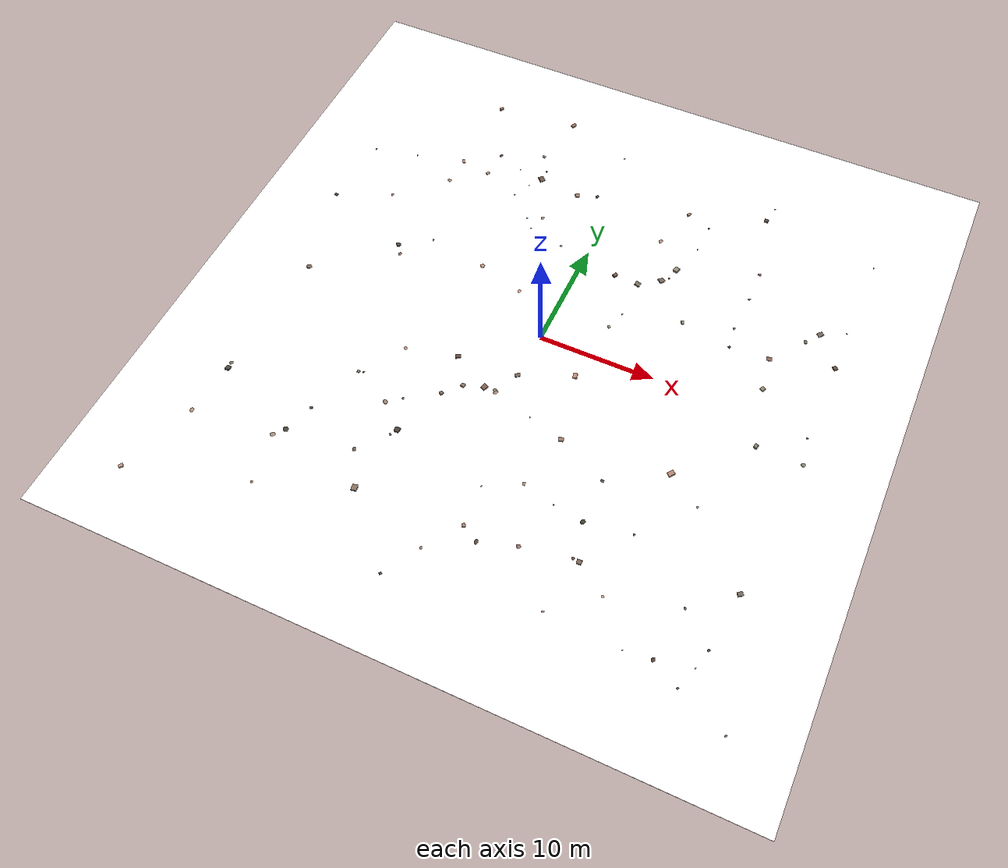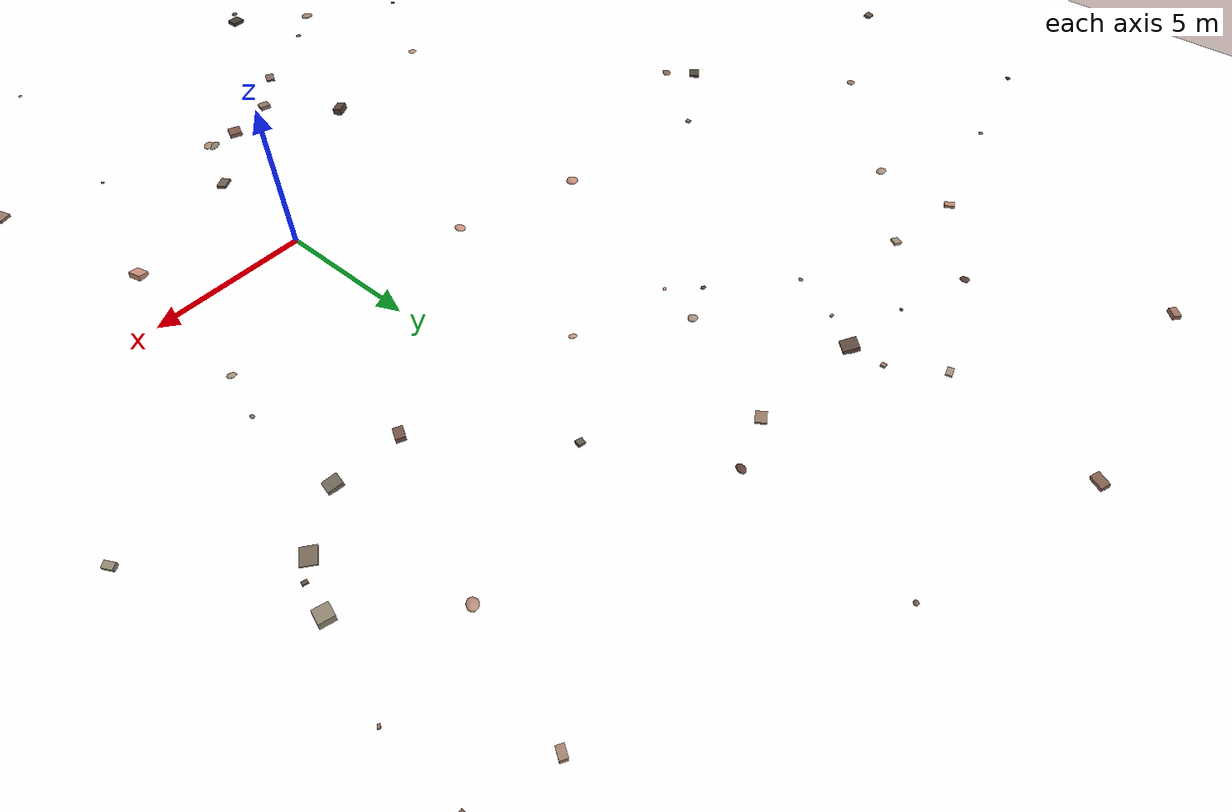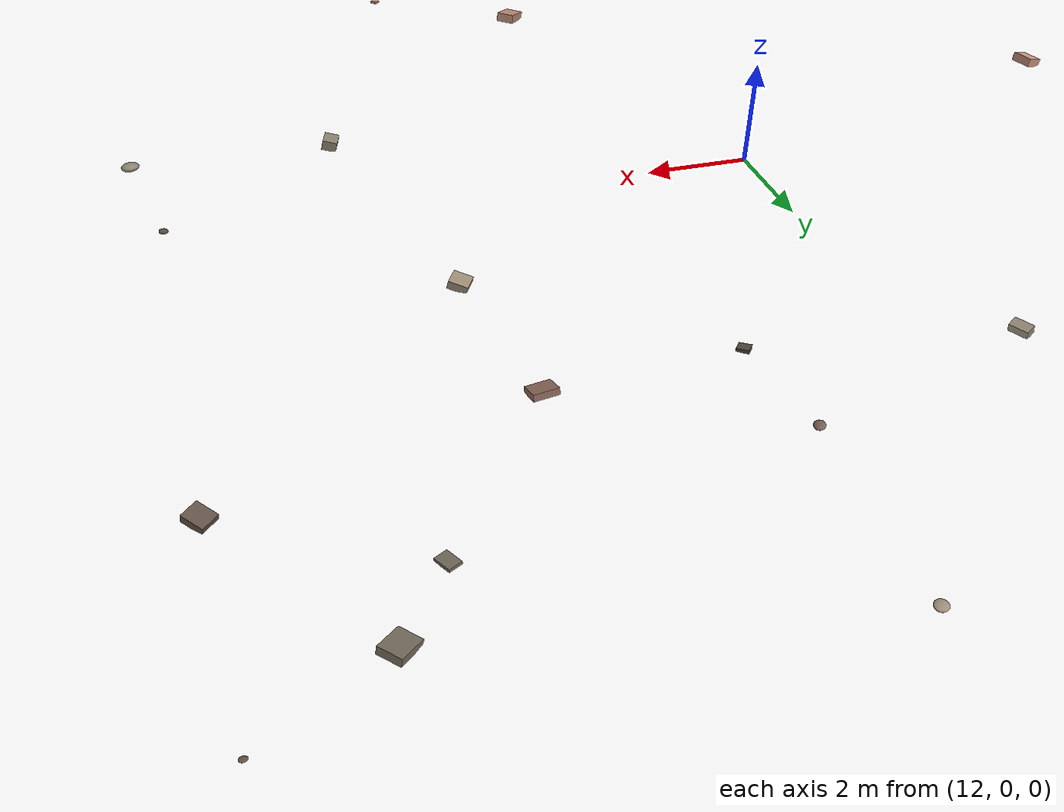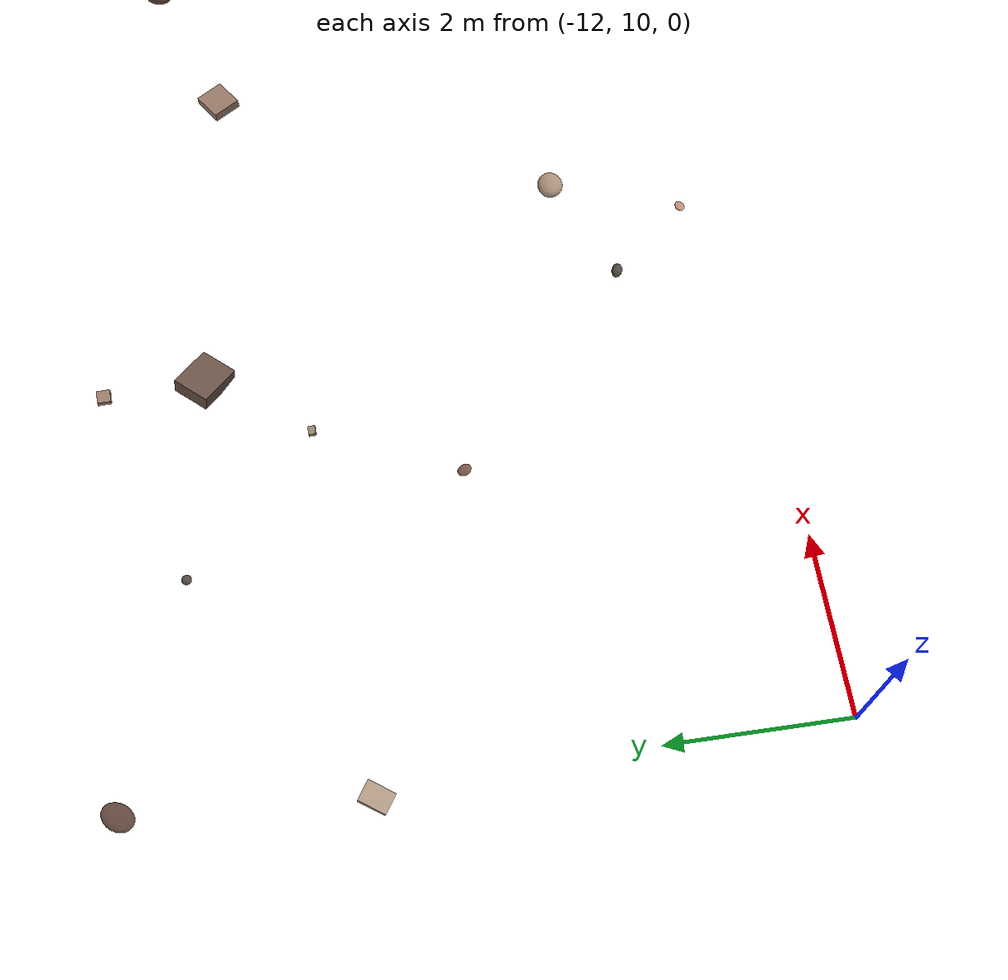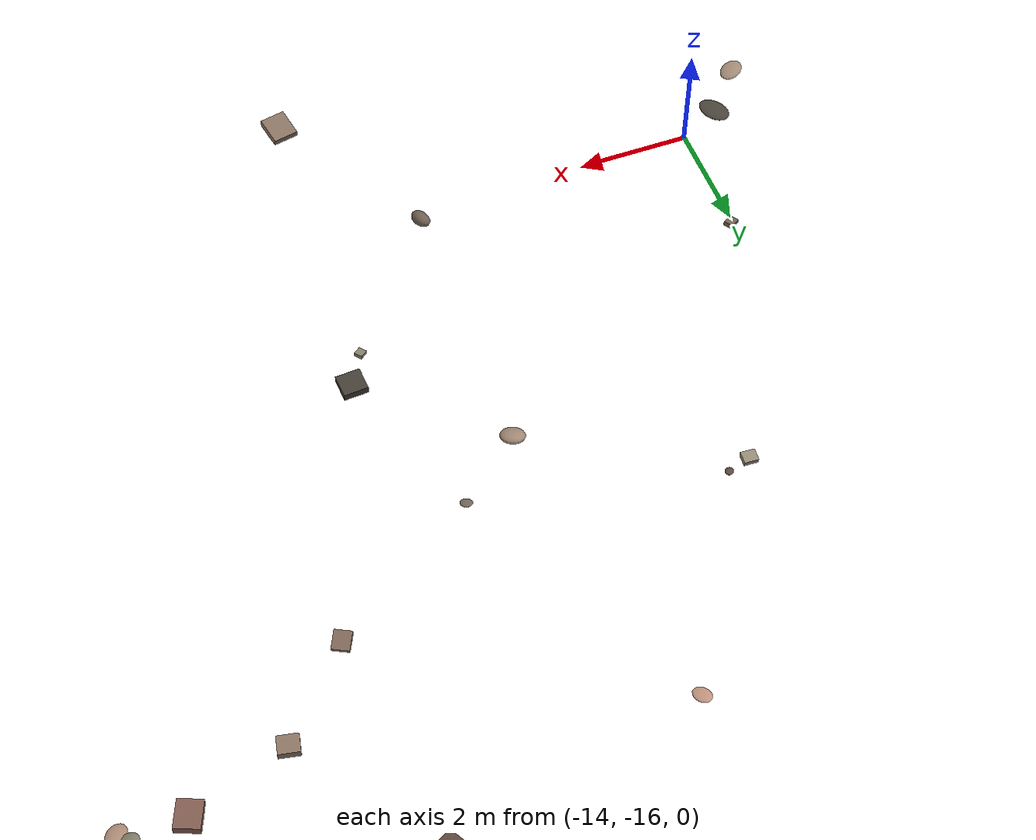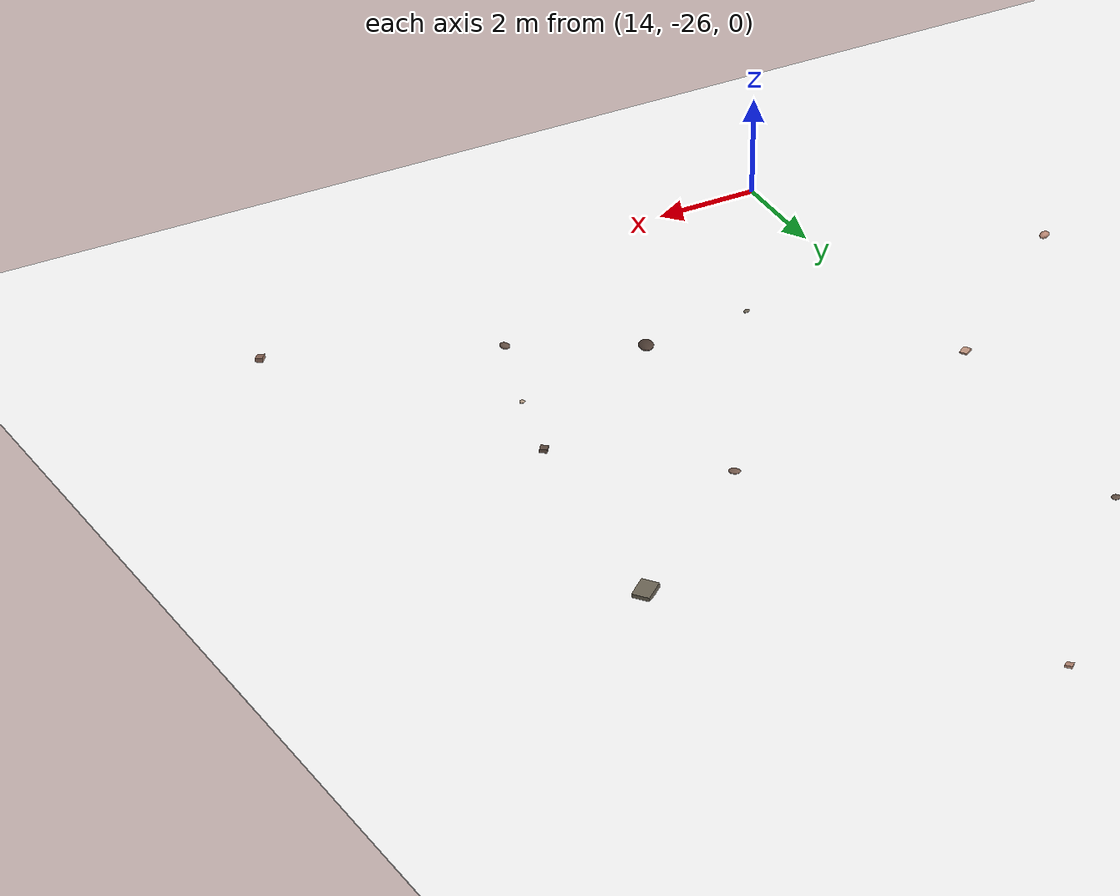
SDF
<?xml version="1.0"?>
<sdf version="1.8">
  <world name="marsyard">

    <plugin filename="gz-sim-physics-system" name="gz::sim::systems::Physics"/>
    <plugin filename="gz-sim-user-commands-system" name="gz::sim::systems::UserCommands"/>
    <plugin filename="gz-sim-scene-broadcaster-system" name="gz::sim::systems::SceneBroadcaster"/>
    <plugin filename="gz-sim-sensors-system" name="gz::sim::systems::Sensors">
      <render_engine>ogre2</render_engine>
    </plugin>
    <plugin filename="gz-sim-imu-system" name="gz::sim::systems::Imu"/>

    <physics name="1ms" type="dart">
      <max_step_size>0.001</max_step_size>
      <real_time_factor>1.0</real_time_factor>
    </physics>

    <gravity>0 0 -9.80665</gravity>

    <light type="directional" name="sun">
      <cast_shadows>true</cast_shadows>
      <pose>0 0 12 0 0 0</pose>
      <diffuse>1.0 0.94 0.86 1</diffuse>
      <specular>0.2 0.2 0.2 1</specular>
      <direction>-0.6 0.35 -0.72</direction>
    </light>

    <scene>
      <ambient>0.45 0.42 0.40 1</ambient>
      <background>0.55 0.42 0.34 1</background>
    </scene>

    <model name="ground_plane">
      <static>true</static>
      <link name="link">
        <!-- Collision stays an infinite plane, as in every other world, so driving
             behaves identically off the textured square. -->
        <collision name="collision">
          <geometry><plane><normal>0 0 1</normal><size>200 200</size></plane></geometry>
          <surface><friction><ode><mu>1.0</mu><mu2>1.0</mu2></ode></friction></surface>
        </collision>
        <visual name="visual">
          <pose>0 0 -0.0100 0 0 0</pose>
          <geometry>
            <box><size>60.0 60.0 0.02</size></box>
          </geometry>
          <material>
            <ambient>0.5 0.45 0.42 1</ambient>
            <diffuse>1 1 1 1</diffuse>
            <pbr>
              <metal>
                <albedo_map>model://MarsyardGround/materials/textures/regolith.png</albedo_map>
                <roughness>0.95</roughness>
                <metalness>0.0</metalness>
              </metal>
            </pbr>
          </material>
        </visual>
      </link>
    </model>

    <model name="rock_000">
      <static>true</static>
      <pose>20.207 8.628 0.025 0.072 0 0.474</pose>
      <link name="link">
        <collision name="collision"><geometry><box><size>0.226 0.302 0.050</size></box></geometry></collision>
        <visual name="visual">
          <geometry><box><size>0.226 0.302 0.050</size></box></geometry>
          <material>
            <ambient>0.177 0.167 0.142 1</ambient>
            <diffuse>0.442 0.417 0.356 1</diffuse>
          </material>
        </visual>
      </link>
    </model>
    <model name="rock_001">
      <static>true</static>
      <pose>5.267 8.508 0.078 0.181 0 1.358</pose>
      <link name="link">
        <collision name="collision"><geometry><box><size>0.398 0.458 0.155</size></box></geometry></collision>
        <visual name="visual">
          <geometry><box><size>0.398 0.458 0.155</size></box></geometry>
          <material>
            <ambient>0.180 0.167 0.143 1</ambient>
            <diffuse>0.450 0.418 0.357 1</diffuse>
          </material>
        </visual>
      </link>
    </model>
    <model name="rock_002">
      <static>true</static>
      <pose>-14.760 -16.409 0.054 0.211 0 3.976</pose>
      <link name="link">
        <collision name="collision"><geometry><ellipsoid><radii>0.214 0.291 0.054</radii></ellipsoid></geometry></collision>
        <visual name="visual">
          <geometry><ellipsoid><radii>0.214 0.291 0.054</radii></ellipsoid></geometry>
          <material>
            <ambient>0.109 0.101 0.086 1</ambient>
            <diffuse>0.273 0.253 0.216 1</diffuse>
          </material>
        </visual>
      </link>
    </model>
    <model name="rock_003">
      <static>true</static>
      <pose>-14.718 -21.523 0.024 0.050 0 0.981</pose>
      <link name="link">
        <collision name="collision"><geometry><ellipsoid><radii>0.105 0.116 0.024</radii></ellipsoid></geometry></collision>
        <visual name="visual">
          <geometry><ellipsoid><radii>0.105 0.116 0.024</radii></ellipsoid></geometry>
          <material>
            <ambient>0.236 0.169 0.144 1</ambient>
            <diffuse>0.589 0.422 0.360 1</diffuse>
          </material>
        </visual>
      </link>
    </model>
    <model name="rock_004">
      <static>true</static>
      <pose>18.540 -21.970 0.054 -0.148 0 4.541</pose>
      <link name="link">
        <collision name="collision"><geometry><ellipsoid><radii>0.191 0.137 0.054</radii></ellipsoid></geometry></collision>
        <visual name="visual">
          <geometry><ellipsoid><radii>0.191 0.137 0.054</radii></ellipsoid></geometry>
          <material>
            <ambient>0.121 0.095 0.081 1</ambient>
            <diffuse>0.302 0.238 0.203 1</diffuse>
          </material>
        </visual>
      </link>
    </model>
    <model name="rock_005">
      <static>true</static>
      <pose>2.372 -7.461 0.028 -0.121 0 2.134</pose>
      <link name="link">
        <collision name="collision"><geometry><ellipsoid><radii>0.065 0.056 0.028</radii></ellipsoid></geometry></collision>
        <visual name="visual">
          <geometry><ellipsoid><radii>0.065 0.056 0.028</radii></ellipsoid></geometry>
          <material>
            <ambient>0.148 0.109 0.093 1</ambient>
            <diffuse>0.370 0.273 0.233 1</diffuse>
          </material>
        </visual>
      </link>
    </model>
    <model name="rock_006">
      <static>true</static>
      <pose>4.728 3.320 0.055 0.137 0 0.838</pose>
      <link name="link">
        <collision name="collision"><geometry><ellipsoid><radii>0.107 0.146 0.055</radii></ellipsoid></geometry></collision>
        <visual name="visual">
          <geometry><ellipsoid><radii>0.107 0.146 0.055</radii></ellipsoid></geometry>
          <material>
            <ambient>0.255 0.229 0.196 1</ambient>
            <diffuse>0.638 0.573 0.489 1</diffuse>
          </material>
        </visual>
      </link>
    </model>
    <model name="rock_007">
      <static>true</static>
      <pose>1.562 -14.606 0.013 0.044 0 6.023</pose>
      <link name="link">
        <collision name="collision"><geometry><ellipsoid><radii>0.056 0.076 0.013</radii></ellipsoid></geometry></collision>
        <visual name="visual">
          <geometry><ellipsoid><radii>0.056 0.076 0.013</radii></ellipsoid></geometry>
          <material>
            <ambient>0.227 0.195 0.166 1</ambient>
            <diffuse>0.568 0.487 0.416 1</diffuse>
          </material>
        </visual>
      </link>
    </model>
    <model name="rock_008">
      <static>true</static>
      <pose>-18.877 8.929 0.048 0.127 0 2.060</pose>
      <link name="link">
        <collision name="collision"><geometry><ellipsoid><radii>0.145 0.118 0.048</radii></ellipsoid></geometry></collision>
        <visual name="visual">
          <geometry><ellipsoid><radii>0.145 0.118 0.048</radii></ellipsoid></geometry>
          <material>
            <ambient>0.242 0.190 0.162 1</ambient>
            <diffuse>0.606 0.474 0.405 1</diffuse>
          </material>
        </visual>
      </link>
    </model>
    <model name="rock_009">
      <static>true</static>
      <pose>16.293 -22.209 0.017 0.129 0 0.653</pose>
      <link name="link">
        <collision name="collision"><geometry><ellipsoid><radii>0.076 0.050 0.017</radii></ellipsoid></geometry></collision>
        <visual name="visual">
          <geometry><ellipsoid><radii>0.076 0.050 0.017</radii></ellipsoid></geometry>
          <material>
            <ambient>0.172 0.159 0.136 1</ambient>
            <diffuse>0.430 0.397 0.339 1</diffuse>
          </material>
        </visual>
      </link>
    </model>
    <model name="rock_010">
      <static>true</static>
      <pose>14.446 -7.632 0.096 0.191 0 5.559</pose>
      <link name="link">
        <collision name="collision"><geometry><box><size>0.387 0.525 0.191</size></box></geometry></collision>
        <visual name="visual">
          <geometry><box><size>0.387 0.525 0.191</size></box></geometry>
          <material>
            <ambient>0.291 0.216 0.185 1</ambient>
            <diffuse>0.729 0.541 0.462 1</diffuse>
          </material>
        </visual>
      </link>
    </model>
    <model name="rock_011">
      <static>true</static>
      <pose>4.112 -2.392 0.087 -0.241 0 1.811</pose>
      <link name="link">
        <collision name="collision"><geometry><box><size>0.434 0.342 0.174</size></box></geometry></collision>
        <visual name="visual">
          <geometry><box><size>0.434 0.342 0.174</size></box></geometry>
          <material>
            <ambient>0.320 0.234 0.199 1</ambient>
            <diffuse>0.801 0.584 0.498 1</diffuse>
          </material>
        </visual>
      </link>
    </model>
    <model name="rock_012">
      <static>true</static>
      <pose>13.751 -13.575 0.026 -0.059 0 5.164</pose>
      <link name="link">
        <collision name="collision"><geometry><ellipsoid><radii>0.082 0.084 0.026</radii></ellipsoid></geometry></collision>
        <visual name="visual">
          <geometry><ellipsoid><radii>0.082 0.084 0.026</radii></ellipsoid></geometry>
          <material>
            <ambient>0.151 0.123 0.105 1</ambient>
            <diffuse>0.377 0.309 0.263 1</diffuse>
          </material>
        </visual>
      </link>
    </model>
    <model name="rock_013">
      <static>true</static>
      <pose>-11.798 -9.109 0.031 0.216 0 5.553</pose>
      <link name="link">
        <collision name="collision"><geometry><ellipsoid><radii>0.070 0.087 0.031</radii></ellipsoid></geometry></collision>
        <visual name="visual">
          <geometry><ellipsoid><radii>0.070 0.087 0.031</radii></ellipsoid></geometry>
          <material>
            <ambient>0.137 0.113 0.096 1</ambient>
            <diffuse>0.343 0.281 0.240 1</diffuse>
          </material>
        </visual>
      </link>
    </model>
    <model name="rock_014">
      <static>true</static>
      <pose>13.115 19.900 0.066 -0.006 0 3.214</pose>
      <link name="link">
        <collision name="collision"><geometry><box><size>0.355 0.300 0.132</size></box></geometry></collision>
        <visual name="visual">
          <geometry><box><size>0.355 0.300 0.132</size></box></geometry>
          <material>
            <ambient>0.139 0.115 0.098 1</ambient>
            <diffuse>0.347 0.288 0.246 1</diffuse>
          </material>
        </visual>
      </link>
    </model>
    <model name="rock_015">
      <static>true</static>
      <pose>-3.810 -6.947 0.070 0.001 0 6.079</pose>
      <link name="link">
        <collision name="collision"><geometry><box><size>0.348 0.306 0.140</size></box></geometry></collision>
        <visual name="visual">
          <geometry><box><size>0.348 0.306 0.140</size></box></geometry>
          <material>
            <ambient>0.218 0.182 0.155 1</ambient>
            <diffuse>0.544 0.455 0.388 1</diffuse>
          </material>
        </visual>
      </link>
    </model>
    <model name="rock_016">
      <static>true</static>
      <pose>-7.769 4.822 0.094 -0.057 0 2.346</pose>
      <link name="link">
        <collision name="collision"><geometry><ellipsoid><radii>0.192 0.195 0.094</radii></ellipsoid></geometry></collision>
        <visual name="visual">
          <geometry><ellipsoid><radii>0.192 0.195 0.094</radii></ellipsoid></geometry>
          <material>
            <ambient>0.309 0.223 0.190 1</ambient>
            <diffuse>0.772 0.557 0.476 1</diffuse>
          </material>
        </visual>
      </link>
    </model>
    <model name="rock_017">
      <static>true</static>
      <pose>14.491 13.838 0.039 0.147 0 6.130</pose>
      <link name="link">
        <collision name="collision"><geometry><ellipsoid><radii>0.147 0.109 0.039</radii></ellipsoid></geometry></collision>
        <visual name="visual">
          <geometry><ellipsoid><radii>0.147 0.109 0.039</radii></ellipsoid></geometry>
          <material>
            <ambient>0.198 0.149 0.127 1</ambient>
            <diffuse>0.496 0.372 0.318 1</diffuse>
          </material>
        </visual>
      </link>
    </model>
    <model name="rock_018">
      <static>true</static>
      <pose>-14.976 3.096 0.041 0.129 0 3.052</pose>
      <link name="link">
        <collision name="collision"><geometry><ellipsoid><radii>0.144 0.172 0.041</radii></ellipsoid></geometry></collision>
        <visual name="visual">
          <geometry><ellipsoid><radii>0.144 0.172 0.041</radii></ellipsoid></geometry>
          <material>
            <ambient>0.212 0.155 0.132 1</ambient>
            <diffuse>0.529 0.387 0.330 1</diffuse>
          </material>
        </visual>
      </link>
    </model>
    <model name="rock_019">
      <static>true</static>
      <pose>4.445 -13.074 0.033 0.244 0 0.175</pose>
      <link name="link">
        <collision name="collision"><geometry><box><size>0.201 0.263 0.066</size></box></geometry></collision>
        <visual name="visual">
          <geometry><box><size>0.201 0.263 0.066</size></box></geometry>
          <material>
            <ambient>0.267 0.207 0.177 1</ambient>
            <diffuse>0.668 0.518 0.442 1</diffuse>
          </material>
        </visual>
      </link>
    </model>
    <model name="rock_020">
      <static>true</static>
      <pose>-6.691 -12.831 0.066 -0.007 0 4.768</pose>
      <link name="link">
        <collision name="collision"><geometry><box><size>0.418 0.426 0.133</size></box></geometry></collision>
        <visual name="visual">
          <geometry><box><size>0.418 0.426 0.133</size></box></geometry>
          <material>
            <ambient>0.106 0.098 0.083 1</ambient>
            <diffuse>0.265 0.244 0.208 1</diffuse>
          </material>
        </visual>
      </link>
    </model>
    <model name="rock_021">
      <static>true</static>
      <pose>-13.952 -13.857 0.043 0.176 0 5.321</pose>
      <link name="link">
        <collision name="collision"><geometry><box><size>0.173 0.202 0.087</size></box></geometry></collision>
        <visual name="visual">
          <geometry><box><size>0.173 0.202 0.087</size></box></geometry>
          <material>
            <ambient>0.178 0.148 0.127 1</ambient>
            <diffuse>0.445 0.371 0.316 1</diffuse>
          </material>
        </visual>
      </link>
    </model>
    <model name="rock_022">
      <static>true</static>
      <pose>-3.505 15.728 0.053 -0.116 0 5.277</pose>
      <link name="link">
        <collision name="collision"><geometry><box><size>0.333 0.369 0.106</size></box></geometry></collision>
        <visual name="visual">
          <geometry><box><size>0.333 0.369 0.106</size></box></geometry>
          <material>
            <ambient>0.236 0.190 0.162 1</ambient>
            <diffuse>0.591 0.475 0.406 1</diffuse>
          </material>
        </visual>
      </link>
    </model>
    <model name="rock_023">
      <static>true</static>
      <pose>24.930 -24.906 0.040 -0.197 0 3.970</pose>
      <link name="link">
        <collision name="collision"><geometry><box><size>0.171 0.142 0.079</size></box></geometry></collision>
        <visual name="visual">
          <geometry><box><size>0.171 0.142 0.079</size></box></geometry>
          <material>
            <ambient>0.226 0.170 0.145 1</ambient>
            <diffuse>0.566 0.424 0.362 1</diffuse>
          </material>
        </visual>
      </link>
    </model>
    <model name="rock_024">
      <static>true</static>
      <pose>3.124 8.604 0.091 -0.053 0 4.211</pose>
      <link name="link">
        <collision name="collision"><geometry><box><size>0.398 0.284 0.181</size></box></geometry></collision>
        <visual name="visual">
          <geometry><box><size>0.398 0.284 0.181</size></box></geometry>
          <material>
            <ambient>0.187 0.135 0.115 1</ambient>
            <diffuse>0.468 0.337 0.288 1</diffuse>
          </material>
        </visual>
      </link>
    </model>
    <model name="rock_025">
      <static>true</static>
      <pose>-11.919 17.414 0.039 0.240 0 5.646</pose>
      <link name="link">
        <collision name="collision"><geometry><ellipsoid><radii>0.137 0.177 0.039</radii></ellipsoid></geometry></collision>
        <visual name="visual">
          <geometry><ellipsoid><radii>0.137 0.177 0.039</radii></ellipsoid></geometry>
          <material>
            <ambient>0.145 0.106 0.090 1</ambient>
            <diffuse>0.363 0.264 0.225 1</diffuse>
          </material>
        </visual>
      </link>
    </model>
    <model name="rock_026">
      <static>true</static>
      <pose>-7.261 16.184 0.086 -0.236 0 3.990</pose>
      <link name="link">
        <collision name="collision"><geometry><box><size>0.431 0.515 0.172</size></box></geometry></collision>
        <visual name="visual">
          <geometry><box><size>0.431 0.515 0.172</size></box></geometry>
          <material>
            <ambient>0.164 0.128 0.109 1</ambient>
            <diffuse>0.409 0.320 0.273 1</diffuse>
          </material>
        </visual>
      </link>
    </model>
    <model name="rock_027">
      <static>true</static>
      <pose>-7.669 -10.018 0.031 -0.110 0 2.704</pose>
      <link name="link">
        <collision name="collision"><geometry><ellipsoid><radii>0.106 0.087 0.031</radii></ellipsoid></geometry></collision>
        <visual name="visual">
          <geometry><ellipsoid><radii>0.106 0.087 0.031</radii></ellipsoid></geometry>
          <material>
            <ambient>0.174 0.154 0.132 1</ambient>
            <diffuse>0.435 0.386 0.329 1</diffuse>
          </material>
        </visual>
      </link>
    </model>
    <model name="rock_028">
      <static>true</static>
      <pose>14.531 10.938 0.038 0.130 0 3.489</pose>
      <link name="link">
        <collision name="collision"><geometry><ellipsoid><radii>0.113 0.098 0.038</radii></ellipsoid></geometry></collision>
        <visual name="visual">
          <geometry><ellipsoid><radii>0.113 0.098 0.038</radii></ellipsoid></geometry>
          <material>
            <ambient>0.240 0.218 0.186 1</ambient>
            <diffuse>0.599 0.544 0.464 1</diffuse>
          </material>
        </visual>
      </link>
    </model>
    <model name="rock_029">
      <static>true</static>
      <pose>-9.792 -5.607 0.032 -0.030 0 3.810</pose>
      <link name="link">
        <collision name="collision"><geometry><ellipsoid><radii>0.125 0.161 0.032</radii></ellipsoid></geometry></collision>
        <visual name="visual">
          <geometry><ellipsoid><radii>0.125 0.161 0.032</radii></ellipsoid></geometry>
          <material>
            <ambient>0.296 0.226 0.193 1</ambient>
            <diffuse>0.740 0.565 0.482 1</diffuse>
          </material>
        </visual>
      </link>
    </model>
    <model name="rock_030">
      <static>true</static>
      <pose>10.358 -17.224 0.058 0.001 0 5.485</pose>
      <link name="link">
        <collision name="collision"><geometry><ellipsoid><radii>0.122 0.103 0.058</radii></ellipsoid></geometry></collision>
        <visual name="visual">
          <geometry><ellipsoid><radii>0.122 0.103 0.058</radii></ellipsoid></geometry>
          <material>
            <ambient>0.188 0.145 0.123 1</ambient>
            <diffuse>0.470 0.361 0.308 1</diffuse>
          </material>
        </visual>
      </link>
    </model>
    <model name="rock_031">
      <static>true</static>
      <pose>-9.546 16.565 0.030 -0.063 0 0.049</pose>
      <link name="link">
        <collision name="collision"><geometry><ellipsoid><radii>0.054 0.054 0.030</radii></ellipsoid></geometry></collision>
        <visual name="visual">
          <geometry><ellipsoid><radii>0.054 0.054 0.030</radii></ellipsoid></geometry>
          <material>
            <ambient>0.128 0.113 0.096 1</ambient>
            <diffuse>0.321 0.281 0.240 1</diffuse>
          </material>
        </visual>
      </link>
    </model>
    <model name="rock_032">
      <static>true</static>
      <pose>3.252 -18.971 0.063 0.040 0 3.271</pose>
      <link name="link">
        <collision name="collision"><geometry><ellipsoid><radii>0.160 0.213 0.063</radii></ellipsoid></geometry></collision>
        <visual name="visual">
          <geometry><ellipsoid><radii>0.160 0.213 0.063</radii></ellipsoid></geometry>
          <material>
            <ambient>0.146 0.105 0.089 1</ambient>
            <diffuse>0.365 0.261 0.223 1</diffuse>
          </material>
        </visual>
      </link>
    </model>
    <model name="rock_033">
      <static>true</static>
      <pose>22.512 -14.824 0.056 0.137 0 2.228</pose>
      <link name="link">
        <collision name="collision"><geometry><box><size>0.339 0.438 0.111</size></box></geometry></collision>
        <visual name="visual">
          <geometry><box><size>0.339 0.438 0.111</size></box></geometry>
          <material>
            <ambient>0.171 0.159 0.136 1</ambient>
            <diffuse>0.428 0.398 0.339 1</diffuse>
          </material>
        </visual>
      </link>
    </model>
    <model name="rock_034">
      <static>true</static>
      <pose>-19.082 14.239 0.043 -0.097 0 4.473</pose>
      <link name="link">
        <collision name="collision"><geometry><ellipsoid><radii>0.084 0.055 0.043</radii></ellipsoid></geometry></collision>
        <visual name="visual">
          <geometry><ellipsoid><radii>0.084 0.055 0.043</radii></ellipsoid></geometry>
          <material>
            <ambient>0.169 0.160 0.136 1</ambient>
            <diffuse>0.422 0.400 0.341 1</diffuse>
          </material>
        </visual>
      </link>
    </model>
    <model name="rock_035">
      <static>true</static>
      <pose>6.279 -18.018 0.065 0.207 0 4.116</pose>
      <link name="link">
        <collision name="collision"><geometry><ellipsoid><radii>0.172 0.208 0.065</radii></ellipsoid></geometry></collision>
        <visual name="visual">
          <geometry><ellipsoid><radii>0.172 0.208 0.065</radii></ellipsoid></geometry>
          <material>
            <ambient>0.237 0.175 0.149 1</ambient>
            <diffuse>0.592 0.436 0.372 1</diffuse>
          </material>
        </visual>
      </link>
    </model>
    <model name="rock_036">
      <static>true</static>
      <pose>19.238 -17.483 0.036 -0.035 0 5.594</pose>
      <link name="link">
        <collision name="collision"><geometry><ellipsoid><radii>0.112 0.085 0.036</radii></ellipsoid></geometry></collision>
        <visual name="visual">
          <geometry><ellipsoid><radii>0.112 0.085 0.036</radii></ellipsoid></geometry>
          <material>
            <ambient>0.182 0.141 0.120 1</ambient>
            <diffuse>0.454 0.352 0.300 1</diffuse>
          </material>
        </visual>
      </link>
    </model>
    <model name="rock_037">
      <static>true</static>
      <pose>-2.160 -6.393 0.069 -0.073 0 2.759</pose>
      <link name="link">
        <collision name="collision"><geometry><box><size>0.409 0.481 0.137</size></box></geometry></collision>
        <visual name="visual">
          <geometry><box><size>0.409 0.481 0.137</size></box></geometry>
          <material>
            <ambient>0.202 0.146 0.124 1</ambient>
            <diffuse>0.505 0.364 0.311 1</diffuse>
          </material>
        </visual>
      </link>
    </model>
    <model name="rock_038">
      <static>true</static>
      <pose>-21.491 -1.422 0.052 0.217 0 2.292</pose>
      <link name="link">
        <collision name="collision"><geometry><box><size>0.308 0.416 0.103</size></box></geometry></collision>
        <visual name="visual">
          <geometry><box><size>0.308 0.416 0.103</size></box></geometry>
          <material>
            <ambient>0.187 0.161 0.137 1</ambient>
            <diffuse>0.468 0.402 0.343 1</diffuse>
          </material>
        </visual>
      </link>
    </model>
    <model name="rock_039">
      <static>true</static>
      <pose>5.350 13.765 0.087 0.003 0 1.081</pose>
      <link name="link">
        <collision name="collision"><geometry><ellipsoid><radii>0.199 0.161 0.087</radii></ellipsoid></geometry></collision>
        <visual name="visual">
          <geometry><ellipsoid><radii>0.199 0.161 0.087</radii></ellipsoid></geometry>
          <material>
            <ambient>0.287 0.222 0.189 1</ambient>
            <diffuse>0.717 0.554 0.473 1</diffuse>
          </material>
        </visual>
      </link>
    </model>
    <model name="rock_040">
      <static>true</static>
      <pose>-1.778 16.328 0.083 0.169 0 4.393</pose>
      <link name="link">
        <collision name="collision"><geometry><ellipsoid><radii>0.177 0.125 0.083</radii></ellipsoid></geometry></collision>
        <visual name="visual">
          <geometry><ellipsoid><radii>0.177 0.125 0.083</radii></ellipsoid></geometry>
          <material>
            <ambient>0.145 0.107 0.091 1</ambient>
            <diffuse>0.364 0.267 0.228 1</diffuse>
          </material>
        </visual>
      </link>
    </model>
    <model name="rock_041">
      <static>true</static>
      <pose>23.112 10.856 0.017 -0.035 0 3.184</pose>
      <link name="link">
        <collision name="collision"><geometry><ellipsoid><radii>0.058 0.046 0.017</radii></ellipsoid></geometry></collision>
        <visual name="visual">
          <geometry><ellipsoid><radii>0.058 0.046 0.017</radii></ellipsoid></geometry>
          <material>
            <ambient>0.145 0.120 0.103 1</ambient>
            <diffuse>0.363 0.300 0.256 1</diffuse>
          </material>
        </visual>
      </link>
    </model>
    <model name="rock_042">
      <static>true</static>
      <pose>13.496 -19.075 0.023 -0.116 0 5.286</pose>
      <link name="link">
        <collision name="collision"><geometry><box><size>0.151 0.181 0.046</size></box></geometry></collision>
        <visual name="visual">
          <geometry><box><size>0.151 0.181 0.046</size></box></geometry>
          <material>
            <ambient>0.303 0.236 0.201 1</ambient>
            <diffuse>0.759 0.589 0.503 1</diffuse>
          </material>
        </visual>
      </link>
    </model>
    <model name="rock_043">
      <static>true</static>
      <pose>-14.799 15.321 0.047 -0.002 0 5.236</pose>
      <link name="link">
        <collision name="collision"><geometry><box><size>0.334 0.215 0.095</size></box></geometry></collision>
        <visual name="visual">
          <geometry><box><size>0.334 0.215 0.095</size></box></geometry>
          <material>
            <ambient>0.297 0.213 0.182 1</ambient>
            <diffuse>0.744 0.532 0.455 1</diffuse>
          </material>
        </visual>
      </link>
    </model>
    <model name="rock_044">
      <static>true</static>
      <pose>23.508 -2.694 0.075 0.106 0 0.288</pose>
      <link name="link">
        <collision name="collision"><geometry><ellipsoid><radii>0.172 0.169 0.075</radii></ellipsoid></geometry></collision>
        <visual name="visual">
          <geometry><ellipsoid><radii>0.172 0.169 0.075</radii></ellipsoid></geometry>
          <material>
            <ambient>0.217 0.208 0.177 1</ambient>
            <diffuse>0.542 0.519 0.443 1</diffuse>
          </material>
        </visual>
      </link>
    </model>
    <model name="rock_045">
      <static>true</static>
      <pose>5.243 5.003 0.044 0.033 0 4.865</pose>
      <link name="link">
        <collision name="collision"><geometry><ellipsoid><radii>0.087 0.057 0.044</radii></ellipsoid></geometry></collision>
        <visual name="visual">
          <geometry><ellipsoid><radii>0.087 0.057 0.044</radii></ellipsoid></geometry>
          <material>
            <ambient>0.198 0.177 0.151 1</ambient>
            <diffuse>0.495 0.441 0.377 1</diffuse>
          </material>
        </visual>
      </link>
    </model>
    <model name="rock_046">
      <static>true</static>
      <pose>-8.909 -15.788 0.107 0.153 0 2.027</pose>
      <link name="link">
        <collision name="collision"><geometry><ellipsoid><radii>0.197 0.127 0.107</radii></ellipsoid></geometry></collision>
        <visual name="visual">
          <geometry><ellipsoid><radii>0.197 0.127 0.107</radii></ellipsoid></geometry>
          <material>
            <ambient>0.174 0.148 0.127 1</ambient>
            <diffuse>0.434 0.371 0.316 1</diffuse>
          </material>
        </visual>
      </link>
    </model>
    <model name="rock_047">
      <static>true</static>
      <pose>-12.097 14.882 0.043 0.161 0 5.689</pose>
      <link name="link">
        <collision name="collision"><geometry><box><size>0.231 0.317 0.086</size></box></geometry></collision>
        <visual name="visual">
          <geometry><box><size>0.231 0.317 0.086</size></box></geometry>
          <material>
            <ambient>0.270 0.236 0.201 1</ambient>
            <diffuse>0.676 0.590 0.503 1</diffuse>
          </material>
        </visual>
      </link>
    </model>
    <model name="rock_048">
      <static>true</static>
      <pose>0.228 12.496 0.043 -0.101 0 1.318</pose>
      <link name="link">
        <collision name="collision"><geometry><box><size>0.198 0.221 0.086</size></box></geometry></collision>
        <visual name="visual">
          <geometry><box><size>0.198 0.221 0.086</size></box></geometry>
          <material>
            <ambient>0.154 0.146 0.125 1</ambient>
            <diffuse>0.384 0.365 0.312 1</diffuse>
          </material>
        </visual>
      </link>
    </model>
    <model name="rock_049">
      <static>true</static>
      <pose>-15.460 -17.233 0.050 0.112 0 2.160</pose>
      <link name="link">
        <collision name="collision"><geometry><ellipsoid><radii>0.175 0.240 0.050</radii></ellipsoid></geometry></collision>
        <visual name="visual">
          <geometry><ellipsoid><radii>0.175 0.240 0.050</radii></ellipsoid></geometry>
          <material>
            <ambient>0.251 0.213 0.182 1</ambient>
            <diffuse>0.627 0.532 0.454 1</diffuse>
          </material>
        </visual>
      </link>
    </model>
    <model name="rock_050">
      <static>true</static>
      <pose>-0.205 -4.234 0.050 0.040 0 0.574</pose>
      <link name="link">
        <collision name="collision"><geometry><box><size>0.430 0.312 0.099</size></box></geometry></collision>
        <visual name="visual">
          <geometry><box><size>0.430 0.312 0.099</size></box></geometry>
          <material>
            <ambient>0.177 0.151 0.129 1</ambient>
            <diffuse>0.444 0.379 0.323 1</diffuse>
          </material>
        </visual>
      </link>
    </model>
    <model name="rock_051">
      <static>true</static>
      <pose>23.196 7.057 0.060 0.158 0 3.900</pose>
      <link name="link">
        <collision name="collision"><geometry><box><size>0.330 0.386 0.121</size></box></geometry></collision>
        <visual name="visual">
          <geometry><box><size>0.330 0.386 0.121</size></box></geometry>
          <material>
            <ambient>0.157 0.133 0.113 1</ambient>
            <diffuse>0.392 0.332 0.283 1</diffuse>
          </material>
        </visual>
      </link>
    </model>
    <model name="rock_052">
      <static>true</static>
      <pose>-2.049 -24.109 0.021 -0.036 0 5.657</pose>
      <link name="link">
        <collision name="collision"><geometry><box><size>0.188 0.182 0.042</size></box></geometry></collision>
        <visual name="visual">
          <geometry><box><size>0.188 0.182 0.042</size></box></geometry>
          <material>
            <ambient>0.120 0.106 0.090 1</ambient>
            <diffuse>0.301 0.264 0.225 1</diffuse>
          </material>
        </visual>
      </link>
    </model>
    <model name="rock_053">
      <static>true</static>
      <pose>7.237 -13.759 0.026 0.206 0 2.421</pose>
      <link name="link">
        <collision name="collision"><geometry><box><size>0.103 0.067 0.052</size></box></geometry></collision>
        <visual name="visual">
          <geometry><box><size>0.103 0.067 0.052</size></box></geometry>
          <material>
            <ambient>0.314 0.228 0.194 1</ambient>
            <diffuse>0.784 0.569 0.486 1</diffuse>
          </material>
        </visual>
      </link>
    </model>
    <model name="rock_054">
      <static>true</static>
      <pose>8.626 14.288 0.021 0.146 0 0.992</pose>
      <link name="link">
        <collision name="collision"><geometry><box><size>0.112 0.074 0.043</size></box></geometry></collision>
        <visual name="visual">
          <geometry><box><size>0.112 0.074 0.043</size></box></geometry>
          <material>
            <ambient>0.236 0.177 0.151 1</ambient>
            <diffuse>0.591 0.442 0.377 1</diffuse>
          </material>
        </visual>
      </link>
    </model>
    <model name="rock_055">
      <static>true</static>
      <pose>-15.582 3.963 0.062 0.089 0 2.207</pose>
      <link name="link">
        <collision name="collision"><geometry><box><size>0.340 0.359 0.125</size></box></geometry></collision>
        <visual name="visual">
          <geometry><box><size>0.340 0.359 0.125</size></box></geometry>
          <material>
            <ambient>0.126 0.110 0.094 1</ambient>
            <diffuse>0.315 0.276 0.235 1</diffuse>
          </material>
        </visual>
      </link>
    </model>
    <model name="rock_056">
      <static>true</static>
      <pose>-1.115 -6.471 0.050 0.011 0 2.298</pose>
      <link name="link">
        <collision name="collision"><geometry><ellipsoid><radii>0.155 0.197 0.050</radii></ellipsoid></geometry></collision>
        <visual name="visual">
          <geometry><ellipsoid><radii>0.155 0.197 0.050</radii></ellipsoid></geometry>
          <material>
            <ambient>0.265 0.211 0.180 1</ambient>
            <diffuse>0.662 0.529 0.451 1</diffuse>
          </material>
        </visual>
      </link>
    </model>
    <model name="rock_057">
      <static>true</static>
      <pose>-2.489 9.717 0.049 -0.016 0 2.462</pose>
      <link name="link">
        <collision name="collision"><geometry><ellipsoid><radii>0.131 0.084 0.049</radii></ellipsoid></geometry></collision>
        <visual name="visual">
          <geometry><ellipsoid><radii>0.131 0.084 0.049</radii></ellipsoid></geometry>
          <material>
            <ambient>0.286 0.235 0.201 1</ambient>
            <diffuse>0.714 0.588 0.502 1</diffuse>
          </material>
        </visual>
      </link>
    </model>
    <model name="rock_058">
      <static>true</static>
      <pose>9.830 -10.375 0.049 0.232 0 6.107</pose>
      <link name="link">
        <collision name="collision"><geometry><box><size>0.265 0.182 0.097</size></box></geometry></collision>
        <visual name="visual">
          <geometry><box><size>0.265 0.182 0.097</size></box></geometry>
          <material>
            <ambient>0.142 0.129 0.110 1</ambient>
            <diffuse>0.355 0.323 0.276 1</diffuse>
          </material>
        </visual>
      </link>
    </model>
    <model name="rock_059">
      <static>true</static>
      <pose>21.114 9.828 0.060 0.215 0 5.461</pose>
      <link name="link">
        <collision name="collision"><geometry><box><size>0.374 0.468 0.120</size></box></geometry></collision>
        <visual name="visual">
          <geometry><box><size>0.374 0.468 0.120</size></box></geometry>
          <material>
            <ambient>0.187 0.172 0.147 1</ambient>
            <diffuse>0.467 0.429 0.366 1</diffuse>
          </material>
        </visual>
      </link>
    </model>
    <model name="rock_060">
      <static>true</static>
      <pose>-13.024 5.692 0.032 -0.086 0 4.776</pose>
      <link name="link">
        <collision name="collision"><geometry><box><size>0.156 0.118 0.064</size></box></geometry></collision>
        <visual name="visual">
          <geometry><box><size>0.156 0.118 0.064</size></box></geometry>
          <material>
            <ambient>0.244 0.181 0.154 1</ambient>
            <diffuse>0.610 0.452 0.386 1</diffuse>
          </material>
        </visual>
      </link>
    </model>
    <model name="rock_061">
      <static>true</static>
      <pose>17.286 -9.468 0.022 0.135 0 5.465</pose>
      <link name="link">
        <collision name="collision"><geometry><box><size>0.139 0.154 0.044</size></box></geometry></collision>
        <visual name="visual">
          <geometry><box><size>0.139 0.154 0.044</size></box></geometry>
          <material>
            <ambient>0.290 0.219 0.187 1</ambient>
            <diffuse>0.724 0.547 0.467 1</diffuse>
          </material>
        </visual>
      </link>
    </model>
    <model name="rock_062">
      <static>true</static>
      <pose>21.438 -21.336 0.029 -0.059 0 3.318</pose>
      <link name="link">
        <collision name="collision"><geometry><ellipsoid><radii>0.054 0.053 0.029</radii></ellipsoid></geometry></collision>
        <visual name="visual">
          <geometry><ellipsoid><radii>0.054 0.053 0.029</radii></ellipsoid></geometry>
          <material>
            <ambient>0.271 0.235 0.201 1</ambient>
            <diffuse>0.678 0.588 0.502 1</diffuse>
          </material>
        </visual>
      </link>
    </model>
    <model name="rock_063">
      <static>true</static>
      <pose>5.465 -8.319 0.057 0.031 0 3.477</pose>
      <link name="link">
        <collision name="collision"><geometry><box><size>0.392 0.356 0.115</size></box></geometry></collision>
        <visual name="visual">
          <geometry><box><size>0.392 0.356 0.115</size></box></geometry>
          <material>
            <ambient>0.237 0.190 0.162 1</ambient>
            <diffuse>0.592 0.475 0.406 1</diffuse>
          </material>
        </visual>
      </link>
    </model>
    <model name="rock_064">
      <static>true</static>
      <pose>6.549 17.744 0.067 -0.023 0 4.165</pose>
      <link name="link">
        <collision name="collision"><geometry><box><size>0.349 0.212 0.134</size></box></geometry></collision>
        <visual name="visual">
          <geometry><box><size>0.349 0.212 0.134</size></box></geometry>
          <material>
            <ambient>0.261 0.209 0.178 1</ambient>
            <diffuse>0.653 0.522 0.446 1</diffuse>
          </material>
        </visual>
      </link>
    </model>
    <model name="rock_065">
      <static>true</static>
      <pose>17.995 5.721 0.059 0.204 0 0.156</pose>
      <link name="link">
        <collision name="collision"><geometry><box><size>0.439 0.317 0.119</size></box></geometry></collision>
        <visual name="visual">
          <geometry><box><size>0.439 0.317 0.119</size></box></geometry>
          <material>
            <ambient>0.216 0.160 0.137 1</ambient>
            <diffuse>0.540 0.401 0.342 1</diffuse>
          </material>
        </visual>
      </link>
    </model>
    <model name="rock_066">
      <static>true</static>
      <pose>-6.521 11.416 0.045 -0.155 0 5.995</pose>
      <link name="link">
        <collision name="collision"><geometry><ellipsoid><radii>0.088 0.060 0.045</radii></ellipsoid></geometry></collision>
        <visual name="visual">
          <geometry><ellipsoid><radii>0.088 0.060 0.045</radii></ellipsoid></geometry>
          <material>
            <ambient>0.121 0.110 0.094 1</ambient>
            <diffuse>0.301 0.275 0.235 1</diffuse>
          </material>
        </visual>
      </link>
    </model>
    <model name="rock_067">
      <static>true</static>
      <pose>10.037 -21.918 0.062 0.143 0 0.385</pose>
      <link name="link">
        <collision name="collision"><geometry><ellipsoid><radii>0.115 0.078 0.062</radii></ellipsoid></geometry></collision>
        <visual name="visual">
          <geometry><ellipsoid><radii>0.115 0.078 0.062</radii></ellipsoid></geometry>
          <material>
            <ambient>0.285 0.209 0.178 1</ambient>
            <diffuse>0.711 0.521 0.445 1</diffuse>
          </material>
        </visual>
      </link>
    </model>
    <model name="rock_068">
      <static>true</static>
      <pose>-8.230 18.894 0.049 0.210 0 1.827</pose>
      <link name="link">
        <collision name="collision"><geometry><box><size>0.195 0.267 0.098</size></box></geometry></collision>
        <visual name="visual">
          <geometry><box><size>0.195 0.267 0.098</size></box></geometry>
          <material>
            <ambient>0.259 0.229 0.195 1</ambient>
            <diffuse>0.647 0.571 0.488 1</diffuse>
          </material>
        </visual>
      </link>
    </model>
    <model name="rock_069">
      <static>true</static>
      <pose>23.318 18.610 0.014 -0.166 0 4.474</pose>
      <link name="link">
        <collision name="collision"><geometry><box><size>0.112 0.078 0.027</size></box></geometry></collision>
        <visual name="visual">
          <geometry><box><size>0.112 0.078 0.027</size></box></geometry>
          <material>
            <ambient>0.175 0.143 0.122 1</ambient>
            <diffuse>0.437 0.358 0.306 1</diffuse>
          </material>
        </visual>
      </link>
    </model>
    <model name="rock_070">
      <static>true</static>
      <pose>-7.026 -13.417 0.034 -0.121 0 2.263</pose>
      <link name="link">
        <collision name="collision"><geometry><box><size>0.147 0.153 0.068</size></box></geometry></collision>
        <visual name="visual">
          <geometry><box><size>0.147 0.153 0.068</size></box></geometry>
          <material>
            <ambient>0.211 0.198 0.169 1</ambient>
            <diffuse>0.527 0.495 0.423 1</diffuse>
          </material>
        </visual>
      </link>
    </model>
    <model name="rock_071">
      <static>true</static>
      <pose>-14.515 22.942 0.074 -0.074 0 0.802</pose>
      <link name="link">
        <collision name="collision"><geometry><box><size>0.374 0.241 0.148</size></box></geometry></collision>
        <visual name="visual">
          <geometry><box><size>0.374 0.241 0.148</size></box></geometry>
          <material>
            <ambient>0.247 0.182 0.155 1</ambient>
            <diffuse>0.616 0.454 0.388 1</diffuse>
          </material>
        </visual>
      </link>
    </model>
    <model name="rock_072">
      <static>true</static>
      <pose>-14.921 12.634 0.051 -0.062 0 4.352</pose>
      <link name="link">
        <collision name="collision"><geometry><ellipsoid><radii>0.149 0.177 0.051</radii></ellipsoid></geometry></collision>
        <visual name="visual">
          <geometry><ellipsoid><radii>0.149 0.177 0.051</radii></ellipsoid></geometry>
          <material>
            <ambient>0.263 0.225 0.192 1</ambient>
            <diffuse>0.658 0.561 0.479 1</diffuse>
          </material>
        </visual>
      </link>
    </model>
    <model name="rock_073">
      <static>true</static>
      <pose>13.357 21.571 0.015 -0.213 0 1.169</pose>
      <link name="link">
        <collision name="collision"><geometry><ellipsoid><radii>0.067 0.083 0.015</radii></ellipsoid></geometry></collision>
        <visual name="visual">
          <geometry><ellipsoid><radii>0.067 0.083 0.015</radii></ellipsoid></geometry>
          <material>
            <ambient>0.174 0.139 0.119 1</ambient>
            <diffuse>0.435 0.349 0.298 1</diffuse>
          </material>
        </visual>
      </link>
    </model>
    <model name="rock_074">
      <static>true</static>
      <pose>-22.163 -12.771 0.036 0.006 0 2.506</pose>
      <link name="link">
        <collision name="collision"><geometry><ellipsoid><radii>0.152 0.176 0.036</radii></ellipsoid></geometry></collision>
        <visual name="visual">
          <geometry><ellipsoid><radii>0.152 0.176 0.036</radii></ellipsoid></geometry>
          <material>
            <ambient>0.185 0.176 0.150 1</ambient>
            <diffuse>0.463 0.439 0.375 1</diffuse>
          </material>
        </visual>
      </link>
    </model>
    <model name="rock_075">
      <static>true</static>
      <pose>-8.795 -10.937 0.083 0.131 0 5.848</pose>
      <link name="link">
        <collision name="collision"><geometry><ellipsoid><radii>0.214 0.174 0.083</radii></ellipsoid></geometry></collision>
        <visual name="visual">
          <geometry><ellipsoid><radii>0.214 0.174 0.083</radii></ellipsoid></geometry>
          <material>
            <ambient>0.246 0.208 0.177 1</ambient>
            <diffuse>0.614 0.520 0.444 1</diffuse>
          </material>
        </visual>
      </link>
    </model>
    <model name="rock_076">
      <static>true</static>
      <pose>7.481 10.224 0.024 0.003 0 4.467</pose>
      <link name="link">
        <collision name="collision"><geometry><box><size>0.119 0.158 0.047</size></box></geometry></collision>
        <visual name="visual">
          <geometry><box><size>0.119 0.158 0.047</size></box></geometry>
          <material>
            <ambient>0.152 0.116 0.099 1</ambient>
            <diffuse>0.380 0.291 0.248 1</diffuse>
          </material>
        </visual>
      </link>
    </model>
    <model name="rock_077">
      <static>true</static>
      <pose>-8.021 15.084 0.027 -0.149 0 0.005</pose>
      <link name="link">
        <collision name="collision"><geometry><box><size>0.100 0.077 0.054</size></box></geometry></collision>
        <visual name="visual">
          <geometry><box><size>0.100 0.077 0.054</size></box></geometry>
          <material>
            <ambient>0.241 0.212 0.181 1</ambient>
            <diffuse>0.602 0.530 0.453 1</diffuse>
          </material>
        </visual>
      </link>
    </model>
    <model name="rock_078">
      <static>true</static>
      <pose>-1.305 21.771 0.039 -0.086 0 4.278</pose>
      <link name="link">
        <collision name="collision"><geometry><ellipsoid><radii>0.080 0.071 0.039</radii></ellipsoid></geometry></collision>
        <visual name="visual">
          <geometry><ellipsoid><radii>0.080 0.071 0.039</radii></ellipsoid></geometry>
          <material>
            <ambient>0.175 0.146 0.124 1</ambient>
            <diffuse>0.438 0.364 0.311 1</diffuse>
          </material>
        </visual>
      </link>
    </model>
    <model name="rock_079">
      <static>true</static>
      <pose>-1.235 -6.299 0.054 0.230 0 1.736</pose>
      <link name="link">
        <collision name="collision"><geometry><ellipsoid><radii>0.149 0.197 0.054</radii></ellipsoid></geometry></collision>
        <visual name="visual">
          <geometry><ellipsoid><radii>0.149 0.197 0.054</radii></ellipsoid></geometry>
          <material>
            <ambient>0.201 0.190 0.162 1</ambient>
            <diffuse>0.502 0.475 0.405 1</diffuse>
          </material>
        </visual>
      </link>
    </model>
    <model name="rock_080">
      <static>true</static>
      <pose>-7.229 -18.733 0.069 -0.111 0 0.202</pose>
      <link name="link">
        <collision name="collision"><geometry><box><size>0.448 0.525 0.137</size></box></geometry></collision>
        <visual name="visual">
          <geometry><box><size>0.448 0.525 0.137</size></box></geometry>
          <material>
            <ambient>0.213 0.179 0.153 1</ambient>
            <diffuse>0.533 0.447 0.382 1</diffuse>
          </material>
        </visual>
      </link>
    </model>
    <model name="rock_081">
      <static>true</static>
      <pose>6.981 9.735 0.055 -0.216 0 5.597</pose>
      <link name="link">
        <collision name="collision"><geometry><box><size>0.447 0.514 0.110</size></box></geometry></collision>
        <visual name="visual">
          <geometry><box><size>0.447 0.514 0.110</size></box></geometry>
          <material>
            <ambient>0.183 0.157 0.134 1</ambient>
            <diffuse>0.457 0.394 0.336 1</diffuse>
          </material>
        </visual>
      </link>
    </model>
    <model name="rock_082">
      <static>true</static>
      <pose>-8.725 13.506 0.022 -0.220 0 0.348</pose>
      <link name="link">
        <collision name="collision"><geometry><ellipsoid><radii>0.064 0.079 0.022</radii></ellipsoid></geometry></collision>
        <visual name="visual">
          <geometry><ellipsoid><radii>0.064 0.079 0.022</radii></ellipsoid></geometry>
          <material>
            <ambient>0.190 0.140 0.119 1</ambient>
            <diffuse>0.475 0.349 0.298 1</diffuse>
          </material>
        </visual>
      </link>
    </model>
    <model name="rock_083">
      <static>true</static>
      <pose>14.363 7.490 0.038 -0.204 0 4.355</pose>
      <link name="link">
        <collision name="collision"><geometry><ellipsoid><radii>0.112 0.091 0.038</radii></ellipsoid></geometry></collision>
        <visual name="visual">
          <geometry><ellipsoid><radii>0.112 0.091 0.038</radii></ellipsoid></geometry>
          <material>
            <ambient>0.188 0.152 0.129 1</ambient>
            <diffuse>0.469 0.379 0.324 1</diffuse>
          </material>
        </visual>
      </link>
    </model>
    <model name="rock_084">
      <static>true</static>
      <pose>21.859 -19.728 0.035 -0.045 0 2.527</pose>
      <link name="link">
        <collision name="collision"><geometry><box><size>0.146 0.172 0.070</size></box></geometry></collision>
        <visual name="visual">
          <geometry><box><size>0.146 0.172 0.070</size></box></geometry>
          <material>
            <ambient>0.151 0.119 0.102 1</ambient>
            <diffuse>0.376 0.299 0.255 1</diffuse>
          </material>
        </visual>
      </link>
    </model>
    <model name="rock_085">
      <static>true</static>
      <pose>-3.708 3.647 0.056 -0.076 0 4.946</pose>
      <link name="link">
        <collision name="collision"><geometry><ellipsoid><radii>0.192 0.134 0.056</radii></ellipsoid></geometry></collision>
        <visual name="visual">
          <geometry><ellipsoid><radii>0.192 0.134 0.056</radii></ellipsoid></geometry>
          <material>
            <ambient>0.322 0.232 0.198 1</ambient>
            <diffuse>0.805 0.579 0.494 1</diffuse>
          </material>
        </visual>
      </link>
    </model>
    <model name="rock_086">
      <static>true</static>
      <pose>9.852 -14.208 0.106 -0.172 0 4.185</pose>
      <link name="link">
        <collision name="collision"><geometry><ellipsoid><radii>0.205 0.174 0.106</radii></ellipsoid></geometry></collision>
        <visual name="visual">
          <geometry><ellipsoid><radii>0.205 0.174 0.106</radii></ellipsoid></geometry>
          <material>
            <ambient>0.102 0.096 0.082 1</ambient>
            <diffuse>0.255 0.241 0.205 1</diffuse>
          </material>
        </visual>
      </link>
    </model>
    <model name="rock_087">
      <static>true</static>
      <pose>-5.754 10.522 0.018 -0.036 0 3.456</pose>
      <link name="link">
        <collision name="collision"><geometry><ellipsoid><radii>0.068 0.054 0.018</radii></ellipsoid></geometry></collision>
        <visual name="visual">
          <geometry><ellipsoid><radii>0.068 0.054 0.018</radii></ellipsoid></geometry>
          <material>
            <ambient>0.299 0.224 0.191 1</ambient>
            <diffuse>0.748 0.559 0.477 1</diffuse>
          </material>
        </visual>
      </link>
    </model>
    <model name="rock_088">
      <static>true</static>
      <pose>-7.304 23.703 0.087 -0.213 0 4.249</pose>
      <link name="link">
        <collision name="collision"><geometry><box><size>0.442 0.283 0.173</size></box></geometry></collision>
        <visual name="visual">
          <geometry><box><size>0.442 0.283 0.173</size></box></geometry>
          <material>
            <ambient>0.219 0.158 0.135 1</ambient>
            <diffuse>0.549 0.396 0.338 1</diffuse>
          </material>
        </visual>
      </link>
    </model>
    <model name="rock_089">
      <static>true</static>
      <pose>-7.283 17.307 0.033 -0.004 0 1.600</pose>
      <link name="link">
        <collision name="collision"><geometry><box><size>0.147 0.147 0.066</size></box></geometry></collision>
        <visual name="visual">
          <geometry><box><size>0.147 0.147 0.066</size></box></geometry>
          <material>
            <ambient>0.239 0.193 0.165 1</ambient>
            <diffuse>0.597 0.483 0.412 1</diffuse>
          </material>
        </visual>
      </link>
    </model>
    <model name="rock_090">
      <static>true</static>
      <pose>-5.071 -8.331 0.058 0.201 0 2.664</pose>
      <link name="link">
        <collision name="collision"><geometry><box><size>0.290 0.317 0.116</size></box></geometry></collision>
        <visual name="visual">
          <geometry><box><size>0.290 0.317 0.116</size></box></geometry>
          <material>
            <ambient>0.195 0.158 0.135 1</ambient>
            <diffuse>0.488 0.395 0.337 1</diffuse>
          </material>
        </visual>
      </link>
    </model>
    <model name="rock_091">
      <static>true</static>
      <pose>8.710 16.982 0.022 0.082 0 3.188</pose>
      <link name="link">
        <collision name="collision"><geometry><box><size>0.106 0.124 0.043</size></box></geometry></collision>
        <visual name="visual">
          <geometry><box><size>0.106 0.124 0.043</size></box></geometry>
          <material>
            <ambient>0.185 0.135 0.115 1</ambient>
            <diffuse>0.462 0.336 0.287 1</diffuse>
          </material>
        </visual>
      </link>
    </model>
    <model name="rock_092">
      <static>true</static>
      <pose>-22.099 -13.352 0.079 -0.153 0 6.216</pose>
      <link name="link">
        <collision name="collision"><geometry><box><size>0.371 0.406 0.157</size></box></geometry></collision>
        <visual name="visual">
          <geometry><box><size>0.371 0.406 0.157</size></box></geometry>
          <material>
            <ambient>0.124 0.110 0.093 1</ambient>
            <diffuse>0.309 0.274 0.234 1</diffuse>
          </material>
        </visual>
      </link>
    </model>
    <model name="rock_093">
      <static>true</static>
      <pose>-22.544 -17.939 0.045 -0.021 0 4.849</pose>
      <link name="link">
        <collision name="collision"><geometry><ellipsoid><radii>0.199 0.163 0.045</radii></ellipsoid></geometry></collision>
        <visual name="visual">
          <geometry><ellipsoid><radii>0.199 0.163 0.045</radii></ellipsoid></geometry>
          <material>
            <ambient>0.276 0.228 0.194 1</ambient>
            <diffuse>0.689 0.570 0.486 1</diffuse>
          </material>
        </visual>
      </link>
    </model>
    <model name="rock_094">
      <static>true</static>
      <pose>18.440 2.689 0.074 0.212 0 4.158</pose>
      <link name="link">
        <collision name="collision"><geometry><box><size>0.344 0.349 0.149</size></box></geometry></collision>
        <visual name="visual">
          <geometry><box><size>0.344 0.349 0.149</size></box></geometry>
          <material>
            <ambient>0.247 0.220 0.188 1</ambient>
            <diffuse>0.618 0.550 0.470 1</diffuse>
          </material>
        </visual>
      </link>
    </model>
    <model name="rock_095">
      <static>true</static>
      <pose>-22.966 13.386 0.022 0.154 0 1.048</pose>
      <link name="link">
        <collision name="collision"><geometry><box><size>0.140 0.105 0.045</size></box></geometry></collision>
        <visual name="visual">
          <geometry><box><size>0.140 0.105 0.045</size></box></geometry>
          <material>
            <ambient>0.131 0.097 0.083 1</ambient>
            <diffuse>0.327 0.242 0.207 1</diffuse>
          </material>
        </visual>
      </link>
    </model>
    <model name="rock_096">
      <static>true</static>
      <pose>7.742 11.312 0.107 -0.025 0 2.858</pose>
      <link name="link">
        <collision name="collision"><geometry><box><size>0.439 0.457 0.214</size></box></geometry></collision>
        <visual name="visual">
          <geometry><box><size>0.439 0.457 0.214</size></box></geometry>
          <material>
            <ambient>0.232 0.212 0.181 1</ambient>
            <diffuse>0.580 0.531 0.453 1</diffuse>
          </material>
        </visual>
      </link>
    </model>
    <model name="rock_097">
      <static>true</static>
      <pose>10.198 6.257 0.081 -0.235 0 5.198</pose>
      <link name="link">
        <collision name="collision"><geometry><box><size>0.327 0.200 0.163</size></box></geometry></collision>
        <visual name="visual">
          <geometry><box><size>0.327 0.200 0.163</size></box></geometry>
          <material>
            <ambient>0.229 0.212 0.181 1</ambient>
            <diffuse>0.572 0.531 0.453 1</diffuse>
          </material>
        </visual>
      </link>
    </model>
    <model name="rock_098">
      <static>true</static>
      <pose>10.893 -17.329 0.093 0.076 0 0.082</pose>
      <link name="link">
        <collision name="collision"><geometry><box><size>0.390 0.326 0.186</size></box></geometry></collision>
        <visual name="visual">
          <geometry><box><size>0.390 0.326 0.186</size></box></geometry>
          <material>
            <ambient>0.196 0.156 0.133 1</ambient>
            <diffuse>0.490 0.389 0.332 1</diffuse>
          </material>
        </visual>
      </link>
    </model>
    <model name="rock_099">
      <static>true</static>
      <pose>20.815 -23.177 0.048 0.137 0 3.674</pose>
      <link name="link">
        <collision name="collision"><geometry><ellipsoid><radii>0.089 0.100 0.048</radii></ellipsoid></geometry></collision>
        <visual name="visual">
          <geometry><ellipsoid><radii>0.089 0.100 0.048</radii></ellipsoid></geometry>
          <material>
            <ambient>0.152 0.122 0.104 1</ambient>
            <diffuse>0.381 0.306 0.261 1</diffuse>
          </material>
        </visual>
      </link>
    </model>
    <model name="rock_100">
      <static>true</static>
      <pose>23.082 -0.262 0.041 0.033 0 4.402</pose>
      <link name="link">
        <collision name="collision"><geometry><ellipsoid><radii>0.077 0.084 0.041</radii></ellipsoid></geometry></collision>
        <visual name="visual">
          <geometry><ellipsoid><radii>0.077 0.084 0.041</radii></ellipsoid></geometry>
          <material>
            <ambient>0.128 0.115 0.098 1</ambient>
            <diffuse>0.320 0.288 0.246 1</diffuse>
          </material>
        </visual>
      </link>
    </model>
    <model name="rock_101">
      <static>true</static>
      <pose>1.794 -18.131 0.065 -0.018 0 0.573</pose>
      <link name="link">
        <collision name="collision"><geometry><box><size>0.254 0.296 0.130</size></box></geometry></collision>
        <visual name="visual">
          <geometry><box><size>0.254 0.296 0.130</size></box></geometry>
          <material>
            <ambient>0.248 0.189 0.162 1</ambient>
            <diffuse>0.620 0.473 0.404 1</diffuse>
          </material>
        </visual>
      </link>
    </model>
    <model name="rock_102">
      <static>true</static>
      <pose>-5.429 -4.588 0.121 0.102 0 0.473</pose>
      <link name="link">
        <collision name="collision"><geometry><box><size>0.448 0.298 0.241</size></box></geometry></collision>
        <visual name="visual">
          <geometry><box><size>0.448 0.298 0.241</size></box></geometry>
          <material>
            <ambient>0.148 0.112 0.095 1</ambient>
            <diffuse>0.369 0.280 0.239 1</diffuse>
          </material>
        </visual>
      </link>
    </model>
    <model name="rock_103">
      <static>true</static>
      <pose>-5.277 11.980 0.071 0.100 0 4.738</pose>
      <link name="link">
        <collision name="collision"><geometry><ellipsoid><radii>0.146 0.160 0.071</radii></ellipsoid></geometry></collision>
        <visual name="visual">
          <geometry><ellipsoid><radii>0.146 0.160 0.071</radii></ellipsoid></geometry>
          <material>
            <ambient>0.265 0.224 0.191 1</ambient>
            <diffuse>0.663 0.560 0.478 1</diffuse>
          </material>
        </visual>
      </link>
    </model>
    <model name="rock_104">
      <static>true</static>
      <pose>-12.197 -9.228 0.051 0.081 0 3.078</pose>
      <link name="link">
        <collision name="collision"><geometry><box><size>0.245 0.206 0.102</size></box></geometry></collision>
        <visual name="visual">
          <geometry><box><size>0.245 0.206 0.102</size></box></geometry>
          <material>
            <ambient>0.234 0.217 0.185 1</ambient>
            <diffuse>0.585 0.543 0.463 1</diffuse>
          </material>
        </visual>
      </link>
    </model>
    <model name="rock_105">
      <static>true</static>
      <pose>-23.526 6.862 0.045 -0.198 0 6.224</pose>
      <link name="link">
        <collision name="collision"><geometry><box><size>0.302 0.252 0.091</size></box></geometry></collision>
        <visual name="visual">
          <geometry><box><size>0.302 0.252 0.091</size></box></geometry>
          <material>
            <ambient>0.151 0.129 0.110 1</ambient>
            <diffuse>0.378 0.322 0.275 1</diffuse>
          </material>
        </visual>
      </link>
    </model>
    <model name="rock_106">
      <static>true</static>
      <pose>-0.270 -21.084 0.081 -0.122 0 4.811</pose>
      <link name="link">
        <collision name="collision"><geometry><ellipsoid><radii>0.151 0.099 0.081</radii></ellipsoid></geometry></collision>
        <visual name="visual">
          <geometry><ellipsoid><radii>0.151 0.099 0.081</radii></ellipsoid></geometry>
          <material>
            <ambient>0.246 0.197 0.168 1</ambient>
            <diffuse>0.615 0.492 0.420 1</diffuse>
          </material>
        </visual>
      </link>
    </model>
    <model name="rock_107">
      <static>true</static>
      <pose>14.624 5.526 0.033 0.092 0 0.874</pose>
      <link name="link">
        <collision name="collision"><geometry><box><size>0.174 0.213 0.066</size></box></geometry></collision>
        <visual name="visual">
          <geometry><box><size>0.174 0.213 0.066</size></box></geometry>
          <material>
            <ambient>0.122 0.112 0.096 1</ambient>
            <diffuse>0.304 0.280 0.239 1</diffuse>
          </material>
        </visual>
      </link>
    </model>
    <model name="rock_108">
      <static>true</static>
      <pose>-24.682 -24.514 0.069 -0.002 0 2.527</pose>
      <link name="link">
        <collision name="collision"><geometry><box><size>0.288 0.373 0.138</size></box></geometry></collision>
        <visual name="visual">
          <geometry><box><size>0.288 0.373 0.138</size></box></geometry>
          <material>
            <ambient>0.290 0.230 0.196 1</ambient>
            <diffuse>0.724 0.575 0.491 1</diffuse>
          </material>
        </visual>
      </link>
    </model>
    <model name="rock_109">
      <static>true</static>
      <pose>19.647 -2.632 0.097 -0.201 0 1.255</pose>
      <link name="link">
        <collision name="collision"><geometry><box><size>0.359 0.284 0.193</size></box></geometry></collision>
        <visual name="visual">
          <geometry><box><size>0.359 0.284 0.193</size></box></geometry>
          <material>
            <ambient>0.215 0.203 0.173 1</ambient>
            <diffuse>0.536 0.507 0.433 1</diffuse>
          </material>
        </visual>
      </link>
    </model>

  </world>
</sdf>
